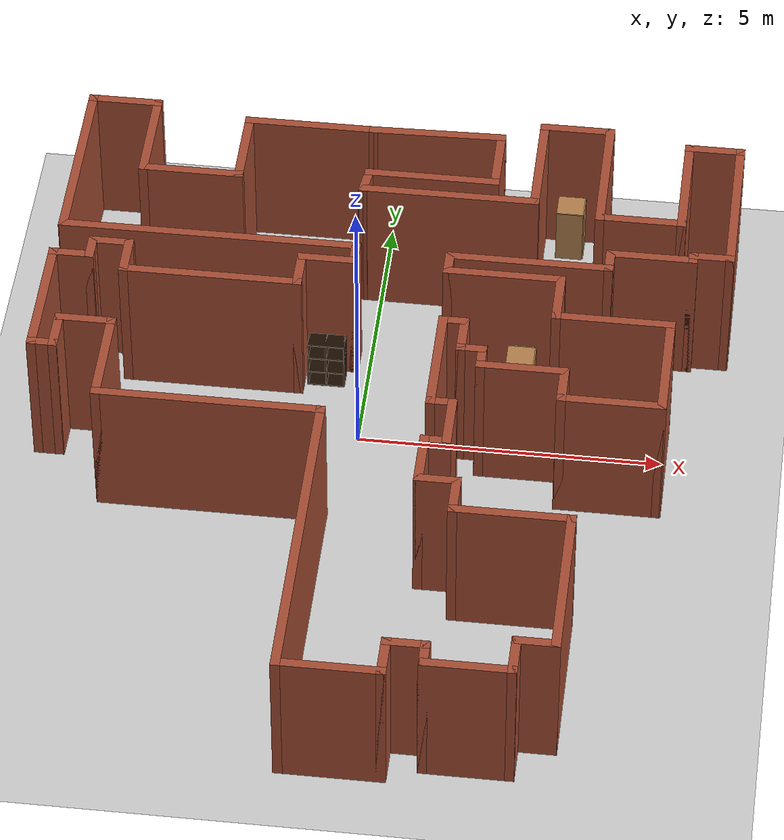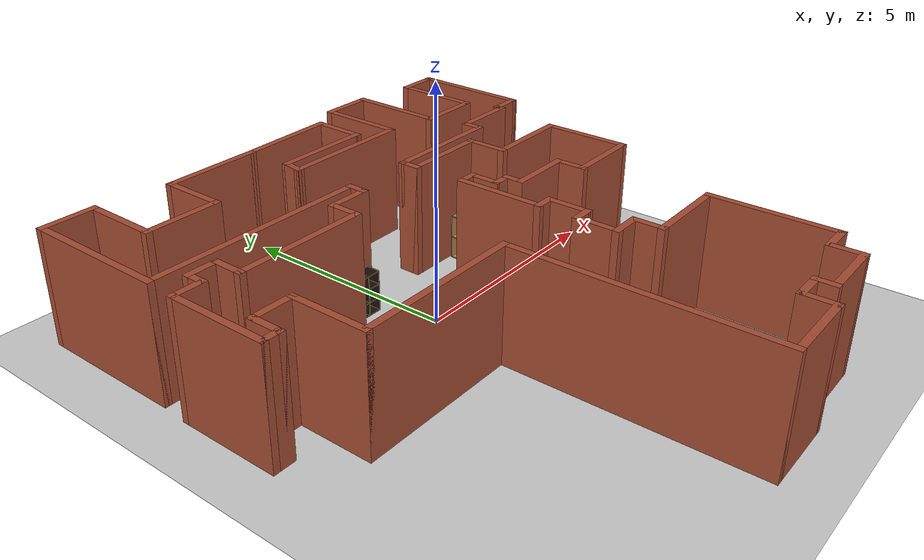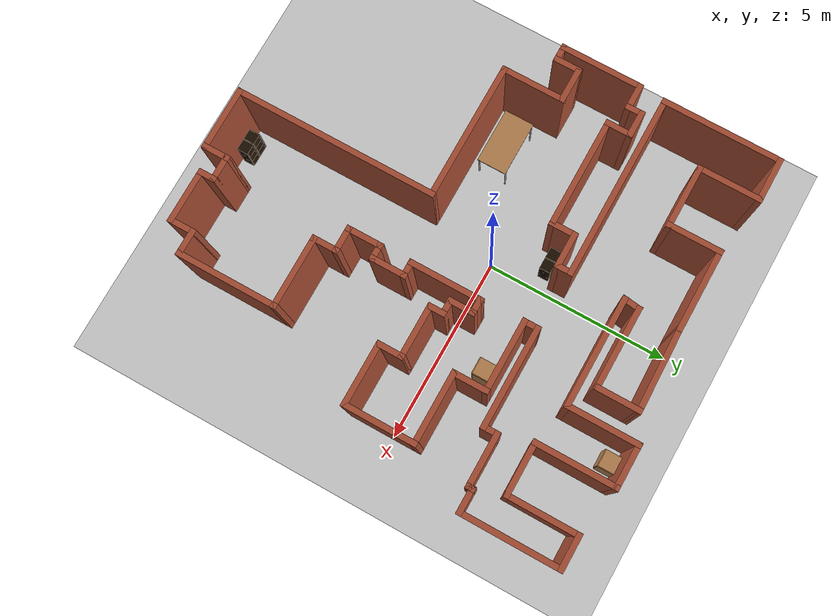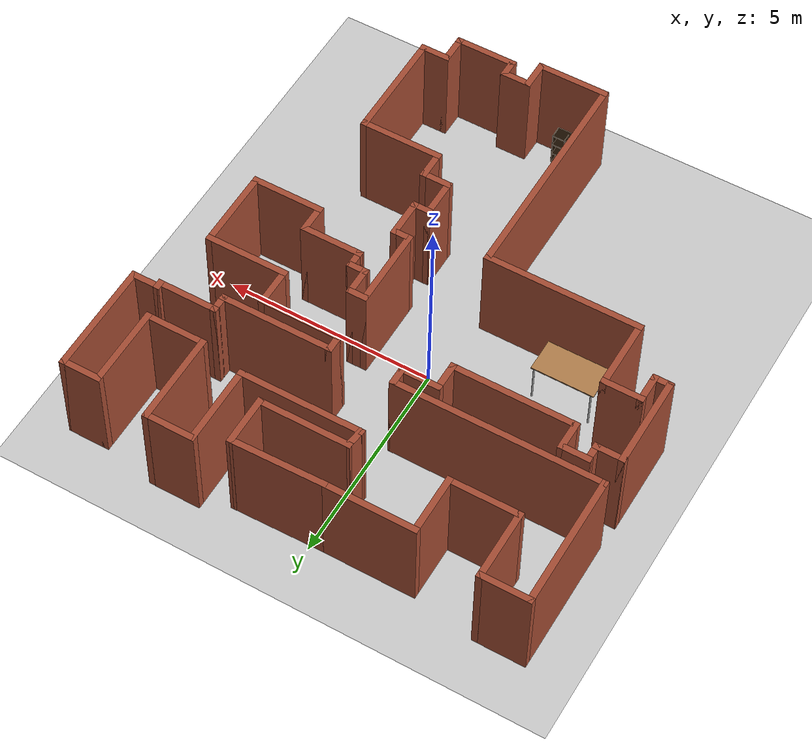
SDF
<sdf version="1.6">
 <world name="default">
  <light name="sun" type="directional">
   <pose>0 0 10 0 -0 0</pose>
   <diffuse>0.8 0.8 0.8 1</diffuse>
   <specular>0.2 0.2 0.2 1</specular>
   <attenuation>
    <range>1000</range>
    <constant>0.9</constant>
    <linear>0.01</linear>
    <quadratic>0.001</quadratic>
   </attenuation>
   <direction>-0.5 0.1 -0.9</direction>
  </light>
  <model name="ground_plane">
   <static>1</static>
   <link name="link">
    <collision name="collision">
     <geometry><plane><normal>0 0 1</normal><size>100 100</size></plane></geometry>
     <surface>
      <contact><collide_bitmask>65535</collide_bitmask></contact>
      <friction><ode><mu>100</mu><mu2>50</mu2></ode></friction>
     </surface>
    </collision>
    <visual name="visual">
     <cast_shadows>0</cast_shadows>
     <geometry><plane><normal>0 0 1</normal><size>100 100</size></plane></geometry>
     <material>
      <script><uri>file://media/materials/scripts/gazebo.material</uri><name>Gazebo/Grey</name></script>
     </material>
    </visual>
   </link>
  </model>
  <gravity>0 0 -9.8</gravity>
  <magnetic_field>6e-06 2.3e-05 -4.2e-05</magnetic_field>
  <atmosphere type="adiabatic"/>
  <physics name="default_physics" default="0" type="ode">
   <max_step_size>0.001</max_step_size>
   <real_time_factor>1</real_time_factor>
   <real_time_update_rate>1000</real_time_update_rate>
  </physics>
  <scene><ambient>0.4 0.4 0.4 1</ambient><background>0.7 0.7 0.7 1</background><shadows>1</shadows></scene>
  <audio><device>default</device></audio>
  <spherical_coordinates>
   <surface_model>EARTH_WGS84</surface_model>
   <latitude_deg>0</latitude_deg>
   <longitude_deg>0</longitude_deg>
   <elevation>0</elevation>
   <heading_deg>0</heading_deg>
  </spherical_coordinates>
  <model name="map_71">
   <pose>0.344292 -0.976267 0 0 -0 0</pose>
   <link name="Wall_0">
    <collision name="Wall_0_Collision">
     <geometry><box><size>2.25 0.15 2.5</size></box></geometry>
     <pose>0 0 1.25 0 -0 0</pose>
    </collision>
    <visual name="Wall_0_Visual">
     <pose>0 0 1.25 0 -0 0</pose>
     <geometry><box><size>2.25 0.15 2.5</size></box></geometry>
     <material>
      <script><uri>file://media/materials/scripts/gazebo.material</uri><name>Gazebo/Bricks</name></script>
      <ambient>1 1 1 1</ambient>
     </material>
     <meta><layer>0</layer></meta>
    </visual>
    <pose>-1.7 5.8 0 0 -0 3.14159</pose>
   </link>
   <link name="Wall_1">
    <collision name="Wall_1_Collision">
     <geometry><box><size>1.5 0.15 2.5</size></box></geometry>
     <pose>0 0 1.25 0 -0 0</pose>
    </collision>
    <visual name="Wall_1_Visual">
     <pose>0 0 1.25 0 -0 0</pose>
     <geometry><box><size>1.5 0.15 2.5</size></box></geometry>
     <material>
      <script><uri>file://media/materials/scripts/gazebo.material</uri><name>Gazebo/Bricks</name></script>
      <ambient>1 1 1 1</ambient>
     </material>
     <meta><layer>0</layer></meta>
    </visual>
    <pose>-2.75 5.125 0 0 -0 -1.5708</pose>
   </link>
   <link name="Wall_10">
    <collision name="Wall_10_Collision">
     <geometry><box><size>3 0.15 2.5</size></box></geometry>
     <pose>0 0 1.25 0 -0 0</pose>
    </collision>
    <visual name="Wall_10_Visual">
     <pose>0 0 1.25 0 -0 0</pose>
     <geometry><box><size>3 0.15 2.5</size></box></geometry>
     <material>
      <script><uri>file://media/materials/scripts/gazebo.material</uri><name>Gazebo/Bricks</name></script>
      <ambient>1 1 1 1</ambient>
     </material>
     <meta><layer>0</layer></meta>
    </visual>
    <pose>-2.875 2 0 0 -0 3.14159</pose>
   </link>
   <link name="Wall_11">
    <collision name="Wall_11_Collision">
     <geometry><box><size>0.75 0.15 2.5</size></box></geometry>
     <pose>0 0 1.25 0 -0 0</pose>
    </collision>
    <visual name="Wall_11_Visual">
     <pose>0 0 1.25 0 -0 0</pose>
     <geometry><box><size>0.75 0.15 2.5</size></box></geometry>
     <material>
      <script><uri>file://media/materials/scripts/gazebo.material</uri><name>Gazebo/Bricks</name></script>
      <ambient>1 1 1 1</ambient>
     </material>
     <meta><layer>0</layer></meta>
    </visual>
    <pose>-4.3 2.3 0 0 -0 1.5708</pose>
   </link>
   <link name="Wall_12">
    <collision name="Wall_12_Collision">
     <geometry><box><size>0.75 0.15 2.5</size></box></geometry>
     <pose>0 0 1.25 0 -0 0</pose>
    </collision>
    <visual name="Wall_12_Visual">
     <pose>0 0 1.25 0 -0 0</pose>
     <geometry><box><size>0.75 0.15 2.5</size></box></geometry>
     <material>
      <script><uri>file://media/materials/scripts/gazebo.material</uri><name>Gazebo/Bricks</name></script>
      <ambient>1 1 1 1</ambient>
     </material>
     <meta><layer>0</layer></meta>
    </visual>
    <pose>-4.6 2.6 0 0 -0 3.14159</pose>
   </link>
   <link name="Wall_13">
    <collision name="Wall_13_Collision">
     <geometry><box><size>0.5 0.15 2.5</size></box></geometry>
     <pose>0 0 1.25 0 -0 0</pose>
    </collision>
    <visual name="Wall_13_Visual">
     <pose>0 0 1.25 0 -0 0</pose>
     <geometry><box><size>0.5 0.15 2.5</size></box></geometry>
     <material>
      <script><uri>file://media/materials/scripts/gazebo.material</uri><name>Gazebo/Bricks</name></script>
      <ambient>1 1 1 1</ambient>
     </material>
     <meta><layer>0</layer></meta>
    </visual>
    <pose>-4.9 2.425 0 0 -0 -1.5708</pose>
   </link>
   <link name="Wall_18">
    <collision name="Wall_18_Collision">
     <geometry><box><size>0.75 0.15 2.5</size></box></geometry>
     <pose>0 0 1.25 0 -0 0</pose>
    </collision>
    <visual name="Wall_18_Visual">
     <pose>0 0 1.25 0 -0 0</pose>
     <geometry><box><size>0.75 0.15 2.5</size></box></geometry>
     <material>
      <script><uri>file://media/materials/scripts/gazebo.material</uri><name>Gazebo/Bricks</name></script>
      <ambient>1 1 1 1</ambient>
     </material>
     <meta><layer>0</layer></meta>
    </visual>
    <pose>-5.2 2.25 0 0 -0 3.14159</pose>
   </link>
   <link name="Wall_19">
    <collision name="Wall_19_Collision">
     <geometry><box><size>2.25 0.15 2.5</size></box></geometry>
     <pose>0 0 1.25 0 -0 0</pose>
    </collision>
    <visual name="Wall_19_Visual">
     <pose>0 0 1.25 0 -0 0</pose>
     <geometry><box><size>2.25 0.15 2.5</size></box></geometry>
     <material>
      <script><uri>file://media/materials/scripts/gazebo.material</uri><name>Gazebo/Bricks</name></script>
      <ambient>1 1 1 1</ambient>
     </material>
     <meta><layer>0</layer></meta>
    </visual>
    <pose>-5.5 1.2 0 0 -0 -1.5708</pose>
   </link>
   <link name="Wall_2">
    <collision name="Wall_2_Collision">
     <geometry><box><size>1.75 0.15 2.5</size></box></geometry>
     <pose>0 0 1.25 0 -0 0</pose>
    </collision>
    <visual name="Wall_2_Visual">
     <pose>0 0 1.25 0 -0 0</pose>
     <geometry><box><size>1.75 0.15 2.5</size></box></geometry>
     <material>
      <script><uri>file://media/materials/scripts/gazebo.material</uri><name>Gazebo/Bricks</name></script>
      <ambient>1 1 1 1</ambient>
     </material>
     <meta><layer>0</layer></meta>
    </visual>
    <pose>-3.55 4.45 0 0 -0 3.14159</pose>
   </link>
   <link name="Wall_20">
    <collision name="Wall_20_Collision">
     <geometry><box><size>0.5 0.15 2.5</size></box></geometry>
     <pose>0 0 1.25 0 -0 0</pose>
    </collision>
    <visual name="Wall_20_Visual">
     <pose>0 0 1.25 0 -0 0</pose>
     <geometry><box><size>0.5 0.15 2.5</size></box></geometry>
     <material>
      <script><uri>file://media/materials/scripts/gazebo.material</uri><name>Gazebo/Bricks</name></script>
      <ambient>1 1 1 1</ambient>
     </material>
     <meta><layer>0</layer></meta>
    </visual>
    <pose>-5.325 0.15 0 0 -0 0</pose>
   </link>
   <link name="Wall_21">
    <collision name="Wall_21_Collision">
     <geometry><box><size>0.75 0.15 2.5</size></box></geometry>
     <pose>0 0 1.25 0 -0 0</pose>
    </collision>
    <visual name="Wall_21_Visual">
     <pose>0 0 1.25 0 -0 0</pose>
     <geometry><box><size>0.75 0.15 2.5</size></box></geometry>
     <material>
      <script><uri>file://media/materials/scripts/gazebo.material</uri><name>Gazebo/Bricks</name></script>
      <ambient>1 1 1 1</ambient>
     </material>
     <meta><layer>0</layer></meta>
    </visual>
    <pose>-5.15 0.45 0 0 -0 1.5708</pose>
   </link>
   <link name="Wall_22">
    <collision name="Wall_22_Collision">
     <geometry><box><size>1 0.15 2.5</size></box></geometry>
     <pose>0 0 1.25 0 -0 0</pose>
    </collision>
    <visual name="Wall_22_Visual">
     <pose>0 0 1.25 0 -0 0</pose>
     <geometry><box><size>1 0.15 2.5</size></box></geometry>
     <material>
      <script><uri>file://media/materials/scripts/gazebo.material</uri><name>Gazebo/Bricks</name></script>
      <ambient>1 1 1 1</ambient>
     </material>
     <meta><layer>0</layer></meta>
    </visual>
    <pose>-4.725 0.75 0 0 -0 0</pose>
   </link>
   <link name="Wall_23">
    <collision name="Wall_23_Collision">
     <geometry><box><size>1.75 0.15 2.5</size></box></geometry>
     <pose>0 0 1.25 0 -0 0</pose>
    </collision>
    <visual name="Wall_23_Visual">
     <pose>0 0 1.25 0 -0 0</pose>
     <geometry><box><size>1.75 0.15 2.5</size></box></geometry>
     <material>
      <script><uri>file://media/materials/scripts/gazebo.material</uri><name>Gazebo/Bricks</name></script>
      <ambient>1 1 1 1</ambient>
     </material>
     <meta><layer>0</layer></meta>
    </visual>
    <pose>-4.3 -0.05 0 0 -0 -1.5708</pose>
   </link>
   <link name="Wall_24">
    <collision name="Wall_24_Collision">
     <geometry><box><size>3.75 0.15 2.5</size></box></geometry>
     <pose>0 0 1.25 0 -0 0</pose>
    </collision>
    <visual name="Wall_24_Visual">
     <pose>0 0 1.25 0 -0 0</pose>
     <geometry><box><size>3.75 0.15 2.5</size></box></geometry>
     <material>
      <script><uri>file://media/materials/scripts/gazebo.material</uri><name>Gazebo/Bricks</name></script>
      <ambient>1 1 1 1</ambient>
     </material>
     <meta><layer>0</layer></meta>
    </visual>
    <pose>-2.5 -0.85 0 0 -0 0</pose>
   </link>
   <link name="Wall_25">
    <collision name="Wall_25_Collision">
     <geometry><box><size>5.5 0.15 2.5</size></box></geometry>
     <pose>0 0 1.25 0 -0 0</pose>
    </collision>
    <visual name="Wall_25_Visual">
     <pose>0 0 1.25 0 -0 0</pose>
     <geometry><box><size>5.5 0.15 2.5</size></box></geometry>
     <material>
      <script><uri>file://media/materials/scripts/gazebo.material</uri><name>Gazebo/Bricks</name></script>
      <ambient>1 1 1 1</ambient>
     </material>
     <meta><layer>0</layer></meta>
    </visual>
    <pose>-0.7 -3.525 0 0 -0 -1.5708</pose>
   </link>
   <link name="Wall_26">
    <collision name="Wall_26_Collision">
     <geometry><box><size>1.75 0.15 2.5</size></box></geometry>
     <pose>0 0 1.25 0 -0 0</pose>
    </collision>
    <visual name="Wall_26_Visual">
     <pose>0 0 1.25 0 -0 0</pose>
     <geometry><box><size>1.75 0.15 2.5</size></box></geometry>
     <material>
      <script><uri>file://media/materials/scripts/gazebo.material</uri><name>Gazebo/Bricks</name></script>
      <ambient>1 1 1 1</ambient>
     </material>
     <meta><layer>0</layer></meta>
    </visual>
    <pose>0.1 -6.2 0 0 -0 0</pose>
   </link>
   <link name="Wall_27">
    <collision name="Wall_27_Collision">
     <geometry><box><size>0.75 0.15 2.5</size></box></geometry>
     <pose>0 0 1.25 0 -0 0</pose>
    </collision>
    <visual name="Wall_27_Visual">
     <pose>0 0 1.25 0 -0 0</pose>
     <geometry><box><size>0.75 0.15 2.5</size></box></geometry>
     <material>
      <script><uri>file://media/materials/scripts/gazebo.material</uri><name>Gazebo/Bricks</name></script>
      <ambient>1 1 1 1</ambient>
     </material>
     <meta><layer>0</layer></meta>
    </visual>
    <pose>0.9 -5.9 0 0 -0 1.5708</pose>
   </link>
   <link name="Wall_28">
    <collision name="Wall_28_Collision">
     <geometry><box><size>0.75 0.15 2.5</size></box></geometry>
     <pose>0 0 1.25 0 -0 0</pose>
    </collision>
    <visual name="Wall_28_Visual">
     <pose>0 0 1.25 0 -0 0</pose>
     <geometry><box><size>0.75 0.15 2.5</size></box></geometry>
     <material>
      <script><uri>file://media/materials/scripts/gazebo.material</uri><name>Gazebo/Bricks</name></script>
      <ambient>1 1 1 1</ambient>
     </material>
     <meta><layer>0</layer></meta>
    </visual>
    <pose>1.2 -5.6 0 0 -0 0</pose>
   </link>
   <link name="Wall_29">
    <collision name="Wall_29_Collision">
     <geometry><box><size>0.5 0.15 2.5</size></box></geometry>
     <pose>0 0 1.25 0 -0 0</pose>
    </collision>
    <visual name="Wall_29_Visual">
     <pose>0 0 1.25 0 -0 0</pose>
     <geometry><box><size>0.5 0.15 2.5</size></box></geometry>
     <material>
      <script><uri>file://media/materials/scripts/gazebo.material</uri><name>Gazebo/Bricks</name></script>
      <ambient>1 1 1 1</ambient>
     </material>
     <meta><layer>0</layer></meta>
    </visual>
    <pose>1.5 -5.775 0 0 -0 -1.5708</pose>
   </link>
   <link name="Wall_3">
    <collision name="Wall_3_Collision">
     <geometry><box><size>1.75 0.15 2.5</size></box></geometry>
     <pose>0 0 1.25 0 -0 0</pose>
    </collision>
    <visual name="Wall_3_Visual">
     <pose>0 0 1.25 0 -0 0</pose>
     <geometry><box><size>1.75 0.15 2.5</size></box></geometry>
     <material>
      <script><uri>file://media/materials/scripts/gazebo.material</uri><name>Gazebo/Bricks</name></script>
      <ambient>1 1 1 1</ambient>
     </material>
     <meta><layer>0</layer></meta>
    </visual>
    <pose>-4.35 5.25 0 0 -0 1.5708</pose>
   </link>
   <link name="Wall_30">
    <collision name="Wall_30_Collision">
     <geometry><box><size>1.5 0.15 2.5</size></box></geometry>
     <pose>0 0 1.25 0 -0 0</pose>
    </collision>
    <visual name="Wall_30_Visual">
     <pose>0 0 1.25 0 -0 0</pose>
     <geometry><box><size>1.5 0.15 2.5</size></box></geometry>
     <material>
      <script><uri>file://media/materials/scripts/gazebo.material</uri><name>Gazebo/Bricks</name></script>
      <ambient>1 1 1 1</ambient>
     </material>
     <meta><layer>0</layer></meta>
    </visual>
    <pose>2.175 -5.95 0 0 -0 0</pose>
   </link>
   <link name="Wall_31">
    <collision name="Wall_31_Collision">
     <geometry><box><size>0.75 0.15 2.5</size></box></geometry>
     <pose>0 0 1.25 0 -0 0</pose>
    </collision>
    <visual name="Wall_31_Visual">
     <pose>0 0 1.25 0 -0 0</pose>
     <geometry><box><size>0.75 0.15 2.5</size></box></geometry>
     <material>
      <script><uri>file://media/materials/scripts/gazebo.material</uri><name>Gazebo/Bricks</name></script>
      <ambient>1 1 1 1</ambient>
     </material>
     <meta><layer>0</layer></meta>
    </visual>
    <pose>2.85 -5.65 0 0 -0 1.5708</pose>
   </link>
   <link name="Wall_32">
    <collision name="Wall_32_Collision">
     <geometry><box><size>0.75 0.15 2.5</size></box></geometry>
     <pose>0 0 1.25 0 -0 0</pose>
    </collision>
    <visual name="Wall_32_Visual">
     <pose>0 0 1.25 0 -0 0</pose>
     <geometry><box><size>0.75 0.15 2.5</size></box></geometry>
     <material>
      <script><uri>file://media/materials/scripts/gazebo.material</uri><name>Gazebo/Bricks</name></script>
      <ambient>1 1 1 1</ambient>
     </material>
     <meta><layer>0</layer></meta>
    </visual>
    <pose>3.15 -5.35 0 0 -0 0</pose>
   </link>
   <link name="Wall_33">
    <collision name="Wall_33_Collision">
     <geometry><box><size>2.75 0.15 2.5</size></box></geometry>
     <pose>0 0 1.25 0 -0 0</pose>
    </collision>
    <visual name="Wall_33_Visual">
     <pose>0 0 1.25 0 -0 0</pose>
     <geometry><box><size>2.75 0.15 2.5</size></box></geometry>
     <material>
      <script><uri>file://media/materials/scripts/gazebo.material</uri><name>Gazebo/Bricks</name></script>
      <ambient>1 1 1 1</ambient>
     </material>
     <meta><layer>0</layer></meta>
    </visual>
    <pose>3.45 -4.05 0 0 -0 1.5708</pose>
   </link>
   <link name="Wall_34">
    <collision name="Wall_34_Collision">
     <geometry><box><size>2 0.15 2.5</size></box></geometry>
     <pose>0 0 1.25 0 -0 0</pose>
    </collision>
    <visual name="Wall_34_Visual">
     <pose>0 0 1.25 0 -0 0</pose>
     <geometry><box><size>2 0.15 2.5</size></box></geometry>
     <material>
      <script><uri>file://media/materials/scripts/gazebo.material</uri><name>Gazebo/Bricks</name></script>
      <ambient>1 1 1 1</ambient>
     </material>
     <meta><layer>0</layer></meta>
    </visual>
    <pose>2.525 -2.75 0 0 -0 3.14159</pose>
   </link>
   <link name="Wall_35">
    <collision name="Wall_35_Collision">
     <geometry><box><size>0.75 0.15 2.5</size></box></geometry>
     <pose>0 0 1.25 0 -0 0</pose>
    </collision>
    <visual name="Wall_35_Visual">
     <pose>0 0 1.25 0 -0 0</pose>
     <geometry><box><size>0.75 0.15 2.5</size></box></geometry>
     <material>
      <script><uri>file://media/materials/scripts/gazebo.material</uri><name>Gazebo/Bricks</name></script>
      <ambient>1 1 1 1</ambient>
     </material>
     <meta><layer>0</layer></meta>
    </visual>
    <pose>1.6 -2.45 0 0 -0 1.5708</pose>
   </link>
   <link name="Wall_36">
    <collision name="Wall_36_Collision">
     <geometry><box><size>0.75 0.15 2.5</size></box></geometry>
     <pose>0 0 1.25 0 -0 0</pose>
    </collision>
    <visual name="Wall_36_Visual">
     <pose>0 0 1.25 0 -0 0</pose>
     <geometry><box><size>0.75 0.15 2.5</size></box></geometry>
     <material>
      <script><uri>file://media/materials/scripts/gazebo.material</uri><name>Gazebo/Bricks</name></script>
      <ambient>1 1 1 1</ambient>
     </material>
     <meta><layer>0</layer></meta>
    </visual>
    <pose>1.3 -2.15 0 0 -0 3.14159</pose>
   </link>
   <link name="Wall_37">
    <collision name="Wall_37_Collision">
     <geometry><box><size>1 0.15 2.5</size></box></geometry>
     <pose>0 0 1.25 0 -0 0</pose>
    </collision>
    <visual name="Wall_37_Visual">
     <pose>0 0 1.25 0 -0 0</pose>
     <geometry><box><size>1 0.15 2.5</size></box></geometry>
     <material>
      <script><uri>file://media/materials/scripts/gazebo.material</uri><name>Gazebo/Bricks</name></script>
      <ambient>1 1 1 1</ambient>
     </material>
     <meta><layer>0</layer></meta>
    </visual>
    <pose>1 -1.725 0 0 -0 1.5708</pose>
   </link>
   <link name="Wall_38">
    <collision name="Wall_38_Collision">
     <geometry><box><size>0.5 0.15 2.5</size></box></geometry>
     <pose>0 0 1.25 0 -0 0</pose>
    </collision>
    <visual name="Wall_38_Visual">
     <pose>0 0 1.25 0 -0 0</pose>
     <geometry><box><size>0.5 0.15 2.5</size></box></geometry>
     <material>
      <script><uri>file://media/materials/scripts/gazebo.material</uri><name>Gazebo/Bricks</name></script>
      <ambient>1 1 1 1</ambient>
     </material>
     <meta><layer>0</layer></meta>
    </visual>
    <pose>1.175 -1.3 0 0 -0 0</pose>
   </link>
   <link name="Wall_39">
    <collision name="Wall_39_Collision">
     <geometry><box><size>1 0.15 2.5</size></box></geometry>
     <pose>0 0 1.25 0 -0 0</pose>
    </collision>
    <visual name="Wall_39_Visual">
     <pose>0 0 1.25 0 -0 0</pose>
     <geometry><box><size>1 0.15 2.5</size></box></geometry>
     <material>
      <script><uri>file://media/materials/scripts/gazebo.material</uri><name>Gazebo/Bricks</name></script>
      <ambient>1 1 1 1</ambient>
     </material>
     <meta><layer>0</layer></meta>
    </visual>
    <pose>1.35 -0.875 0 0 -0 1.5708</pose>
   </link>
   <link name="Wall_4">
    <collision name="Wall_4_Collision">
     <geometry><box><size>1.25 0.15 2.5</size></box></geometry>
     <pose>0 0 1.25 0 -0 0</pose>
    </collision>
    <visual name="Wall_4_Visual">
     <pose>0 0 1.25 0 -0 0</pose>
     <geometry><box><size>1.25 0.15 2.5</size></box></geometry>
     <material>
      <script><uri>file://media/materials/scripts/gazebo.material</uri><name>Gazebo/Bricks</name></script>
      <ambient>1 1 1 1</ambient>
     </material>
     <meta><layer>0</layer></meta>
    </visual>
    <pose>-4.9 6.05 0 0 -0 3.14159</pose>
   </link>
   <link name="Wall_40">
    <collision name="Wall_40_Collision">
     <geometry><box><size>0.5 0.15 2.5</size></box></geometry>
     <pose>0 0 1.25 0 -0 0</pose>
    </collision>
    <visual name="Wall_40_Visual">
     <pose>0 0 1.25 0 -0 0</pose>
     <geometry><box><size>0.5 0.15 2.5</size></box></geometry>
     <material>
      <script><uri>file://media/materials/scripts/gazebo.material</uri><name>Gazebo/Bricks</name></script>
      <ambient>1 1 1 1</ambient>
     </material>
     <meta><layer>0</layer></meta>
    </visual>
    <pose>1.175 -0.45 0 0 -0 3.14159</pose>
   </link>
   <link name="Wall_41">
    <collision name="Wall_41_Collision">
     <geometry><box><size>2 0.15 2.5</size></box></geometry>
     <pose>0 0 1.25 0 -0 0</pose>
    </collision>
    <visual name="Wall_41_Visual">
     <pose>0 0 1.25 0 -0 0</pose>
     <geometry><box><size>2 0.15 2.5</size></box></geometry>
     <material>
      <script><uri>file://media/materials/scripts/gazebo.material</uri><name>Gazebo/Bricks</name></script>
      <ambient>1 1 1 1</ambient>
     </material>
     <meta><layer>0</layer></meta>
    </visual>
    <pose>1 0.475 0 0 -0 1.5708</pose>
   </link>
   <link name="Wall_42">
    <collision name="Wall_42_Collision">
     <geometry><box><size>0.5 0.15 2.5</size></box></geometry>
     <pose>0 0 1.25 0 -0 0</pose>
    </collision>
    <visual name="Wall_42_Visual">
     <pose>0 0 1.25 0 -0 0</pose>
     <geometry><box><size>0.5 0.15 2.5</size></box></geometry>
     <material>
      <script><uri>file://media/materials/scripts/gazebo.material</uri><name>Gazebo/Bricks</name></script>
      <ambient>1 1 1 1</ambient>
     </material>
     <meta><layer>0</layer></meta>
    </visual>
    <pose>1.175 1.4 0 0 -0 0</pose>
   </link>
   <link name="Wall_43">
    <collision name="Wall_43_Collision">
     <geometry><box><size>0.75 0.15 2.5</size></box></geometry>
     <pose>0 0 1.25 0 -0 0</pose>
    </collision>
    <visual name="Wall_43_Visual">
     <pose>0 0 1.25 0 -0 0</pose>
     <geometry><box><size>0.75 0.15 2.5</size></box></geometry>
     <material>
      <script><uri>file://media/materials/scripts/gazebo.material</uri><name>Gazebo/Bricks</name></script>
      <ambient>1 1 1 1</ambient>
     </material>
     <meta><layer>0</layer></meta>
    </visual>
    <pose>1.35 1.1 0 0 -0 -1.5708</pose>
   </link>
   <link name="Wall_44">
    <collision name="Wall_44_Collision">
     <geometry><box><size>0.5 0.15 2.5</size></box></geometry>
     <pose>0 0 1.25 0 -0 0</pose>
    </collision>
    <visual name="Wall_44_Visual">
     <pose>0 0 1.25 0 -0 0</pose>
     <geometry><box><size>0.5 0.15 2.5</size></box></geometry>
     <material>
      <script><uri>file://media/materials/scripts/gazebo.material</uri><name>Gazebo/Bricks</name></script>
      <ambient>1 1 1 1</ambient>
     </material>
     <meta><layer>0</layer></meta>
    </visual>
    <pose>1.525 0.8 0 0 -0 0</pose>
   </link>
   <link name="Wall_45">
    <collision name="Wall_45_Collision">
     <geometry><box><size>0.5 0.15 2.5</size></box></geometry>
     <pose>0 0 1.25 0 -0 0</pose>
    </collision>
    <visual name="Wall_45_Visual">
     <pose>0 0 1.25 0 -0 0</pose>
     <geometry><box><size>0.5 0.15 2.5</size></box></geometry>
     <material>
      <script><uri>file://media/materials/scripts/gazebo.material</uri><name>Gazebo/Bricks</name></script>
      <ambient>1 1 1 1</ambient>
     </material>
     <meta><layer>0</layer></meta>
    </visual>
    <pose>1.7 0.625 0 0 -0 -1.5708</pose>
   </link>
   <link name="Wall_46">
    <collision name="Wall_46_Collision">
     <geometry><box><size>1.5 0.15 2.5</size></box></geometry>
     <pose>0 0 1.25 0 -0 0</pose>
    </collision>
    <visual name="Wall_46_Visual">
     <pose>0 0 1.25 0 -0 0</pose>
     <geometry><box><size>1.5 0.15 2.5</size></box></geometry>
     <material>
      <script><uri>file://media/materials/scripts/gazebo.material</uri><name>Gazebo/Bricks</name></script>
      <ambient>1 1 1 1</ambient>
     </material>
     <meta><layer>0</layer></meta>
    </visual>
    <pose>2.375 0.45 0 0 -0 0</pose>
   </link>
   <link name="Wall_47">
    <collision name="Wall_47_Collision">
     <geometry><box><size>0.75 0.15 2.5</size></box></geometry>
     <pose>0 0 1.25 0 -0 0</pose>
    </collision>
    <visual name="Wall_47_Visual">
     <pose>0 0 1.25 0 -0 0</pose>
     <geometry><box><size>0.75 0.15 2.5</size></box></geometry>
     <material>
      <script><uri>file://media/materials/scripts/gazebo.material</uri><name>Gazebo/Bricks</name></script>
      <ambient>1 1 1 1</ambient>
     </material>
     <meta><layer>0</layer></meta>
    </visual>
    <pose>3.05 0.15 0 0 -0 -1.5708</pose>
   </link>
   <link name="Wall_48">
    <collision name="Wall_48_Collision">
     <geometry><box><size>1.75 0.15 2.5</size></box></geometry>
     <pose>0 0 1.25 0 -0 0</pose>
    </collision>
    <visual name="Wall_48_Visual">
     <pose>0 0 1.25 0 -0 0</pose>
     <geometry><box><size>1.75 0.15 2.5</size></box></geometry>
     <material>
      <script><uri>file://media/materials/scripts/gazebo.material</uri><name>Gazebo/Bricks</name></script>
      <ambient>1 1 1 1</ambient>
     </material>
     <meta><layer>0</layer></meta>
    </visual>
    <pose>3.85 -0.15 0 0 -0 0</pose>
   </link>
   <link name="Wall_49">
    <collision name="Wall_49_Collision">
     <geometry><box><size>2 0.15 2.5</size></box></geometry>
     <pose>0 0 1.25 0 -0 0</pose>
    </collision>
    <visual name="Wall_49_Visual">
     <pose>0 0 1.25 0 -0 0</pose>
     <geometry><box><size>2 0.15 2.5</size></box></geometry>
     <material>
      <script><uri>file://media/materials/scripts/gazebo.material</uri><name>Gazebo/Bricks</name></script>
      <ambient>1 1 1 1</ambient>
     </material>
     <meta><layer>0</layer></meta>
    </visual>
    <pose>4.65 0.775 0 0 -0 1.5708</pose>
   </link>
   <link name="Wall_5">
    <collision name="Wall_5_Collision">
     <geometry><box><size>3.25 0.15 2.5</size></box></geometry>
     <pose>0 0 1.25 0 -0 0</pose>
    </collision>
    <visual name="Wall_5_Visual">
     <pose>0 0 1.25 0 -0 0</pose>
     <geometry><box><size>3.25 0.15 2.5</size></box></geometry>
     <material>
      <script><uri>file://media/materials/scripts/gazebo.material</uri><name>Gazebo/Bricks</name></script>
      <ambient>1 1 1 1</ambient>
     </material>
     <meta><layer>0</layer></meta>
    </visual>
    <pose>-5.45 4.5 0 0 -0 -1.5708</pose>
   </link>
   <link name="Wall_50">
    <collision name="Wall_50_Collision">
     <geometry><box><size>2 0.15 2.5</size></box></geometry>
     <pose>0 0 1.25 0 -0 0</pose>
    </collision>
    <visual name="Wall_50_Visual">
     <pose>0 0 1.25 0 -0 0</pose>
     <geometry><box><size>2 0.15 2.5</size></box></geometry>
     <material>
      <script><uri>file://media/materials/scripts/gazebo.material</uri><name>Gazebo/Bricks</name></script>
      <ambient>1 1 1 1</ambient>
     </material>
     <meta><layer>0</layer></meta>
    </visual>
    <pose>3.725 1.7 0 0 -0 3.14159</pose>
   </link>
   <link name="Wall_51">
    <collision name="Wall_51_Collision">
     <geometry><box><size>1 0.15 2.5</size></box></geometry>
     <pose>0 0 1.25 0 -0 0</pose>
    </collision>
    <visual name="Wall_51_Visual">
     <pose>0 0 1.25 0 -0 0</pose>
     <geometry><box><size>1 0.15 2.5</size></box></geometry>
     <material>
      <script><uri>file://media/materials/scripts/gazebo.material</uri><name>Gazebo/Bricks</name></script>
      <ambient>1 1 1 1</ambient>
     </material>
     <meta><layer>0</layer></meta>
    </visual>
    <pose>2.8 2.125 0 0 -0 1.5708</pose>
   </link>
   <link name="Wall_52">
    <collision name="Wall_52_Collision">
     <geometry><box><size>2 0.15 2.5</size></box></geometry>
     <pose>0 0 1.25 0 -0 0</pose>
    </collision>
    <visual name="Wall_52_Visual">
     <pose>0 0 1.25 0 -0 0</pose>
     <geometry><box><size>2 0.15 2.5</size></box></geometry>
     <material>
      <script><uri>file://media/materials/scripts/gazebo.material</uri><name>Gazebo/Bricks</name></script>
      <ambient>1 1 1 1</ambient>
     </material>
     <meta><layer>0</layer></meta>
    </visual>
    <pose>1.875 2.55 0 0 -0 3.14159</pose>
   </link>
   <link name="Wall_53">
    <collision name="Wall_53_Collision">
     <geometry><box><size>0.5 0.15 2.5</size></box></geometry>
     <pose>0 0 1.25 0 -0 0</pose>
    </collision>
    <visual name="Wall_53_Visual">
     <pose>0 0 1.25 0 -0 0</pose>
     <geometry><box><size>0.5 0.15 2.5</size></box></geometry>
     <material>
      <script><uri>file://media/materials/scripts/gazebo.material</uri><name>Gazebo/Bricks</name></script>
      <ambient>1 1 1 1</ambient>
     </material>
     <meta><layer>0</layer></meta>
    </visual>
    <pose>0.95 2.725 0 0 -0 1.5708</pose>
   </link>
   <link name="Wall_54">
    <collision name="Wall_54_Collision">
     <geometry><box><size>2.75 0.15 2.5</size></box></geometry>
     <pose>0 0 1.25 0 -0 0</pose>
    </collision>
    <visual name="Wall_54_Visual">
     <pose>0 0 1.25 0 -0 0</pose>
     <geometry><box><size>2.75 0.15 2.5</size></box></geometry>
     <material>
      <script><uri>file://media/materials/scripts/gazebo.material</uri><name>Gazebo/Bricks</name></script>
      <ambient>1 1 1 1</ambient>
     </material>
     <meta><layer>0</layer></meta>
    </visual>
    <pose>2.25 2.9 0 0 -0 0</pose>
   </link>
   <link name="Wall_55">
    <collision name="Wall_55_Collision">
     <geometry><box><size>0.5 0.15 2.5</size></box></geometry>
     <pose>0 0 1.25 0 -0 0</pose>
    </collision>
    <visual name="Wall_55_Visual">
     <pose>0 0 1.25 0 -0 0</pose>
     <geometry><box><size>0.5 0.15 2.5</size></box></geometry>
     <material>
      <script><uri>file://media/materials/scripts/gazebo.material</uri><name>Gazebo/Bricks</name></script>
      <ambient>1 1 1 1</ambient>
     </material>
     <meta><layer>0</layer></meta>
    </visual>
    <pose>3.55 3.075 0 0 -0 1.5708</pose>
   </link>
   <link name="Wall_56">
    <collision name="Wall_56_Collision">
     <geometry><box><size>1.5 0.15 2.5</size></box></geometry>
     <pose>0 0 1.25 0 -0 0</pose>
    </collision>
    <visual name="Wall_56_Visual">
     <pose>0 0 1.25 0 -0 0</pose>
     <geometry><box><size>1.5 0.15 2.5</size></box></geometry>
     <material>
      <script><uri>file://media/materials/scripts/gazebo.material</uri><name>Gazebo/Bricks</name></script>
      <ambient>1 1 1 1</ambient>
     </material>
     <meta><layer>0</layer></meta>
    </visual>
    <pose>4.225 3.25 0 0 -0 0</pose>
   </link>
   <link name="Wall_57">
    <collision name="Wall_57_Collision">
     <geometry><box><size>0.25 0.15 2.5</size></box></geometry>
     <pose>0 0 1.25 0 -0 0</pose>
    </collision>
    <visual name="Wall_57_Visual">
     <pose>0 0 1.25 0 -0 0</pose>
     <geometry><box><size>0.25 0.15 2.5</size></box></geometry>
     <material>
      <script><uri>file://media/materials/scripts/gazebo.material</uri><name>Gazebo/Bricks</name></script>
      <ambient>1 1 1 1</ambient>
     </material>
     <meta><layer>0</layer></meta>
    </visual>
    <pose>4.9 3.3 0 0 -0 1.5708</pose>
   </link>
   <link name="Wall_58">
    <collision name="Wall_58_Collision">
     <geometry><box><size>0.75 0.15 2.5</size></box></geometry>
     <pose>0 0 1.25 0 -0 0</pose>
    </collision>
    <visual name="Wall_58_Visual">
     <pose>0 0 1.25 0 -0 0</pose>
     <geometry><box><size>0.75 0.15 2.5</size></box></geometry>
     <material>
      <script><uri>file://media/materials/scripts/gazebo.material</uri><name>Gazebo/Bricks</name></script>
      <ambient>1 1 1 1</ambient>
     </material>
     <meta><layer>0</layer></meta>
    </visual>
    <pose>5.2 3.35 0 0 -0 0</pose>
   </link>
   <link name="Wall_59">
    <collision name="Wall_59_Collision">
     <geometry><box><size>2.75 0.15 2.5</size></box></geometry>
     <pose>0 0 1.25 0 -0 0</pose>
    </collision>
    <visual name="Wall_59_Visual">
     <pose>0 0 1.25 0 -0 0</pose>
     <geometry><box><size>2.75 0.15 2.5</size></box></geometry>
     <material>
      <script><uri>file://media/materials/scripts/gazebo.material</uri><name>Gazebo/Bricks</name></script>
      <ambient>1 1 1 1</ambient>
     </material>
     <meta><layer>0</layer></meta>
    </visual>
    <pose>5.5 4.65 0 0 -0 1.5708</pose>
   </link>
   <link name="Wall_6">
    <collision name="Wall_6_Collision">
     <geometry><box><size>5 0.15 2.5</size></box></geometry>
     <pose>0 0 1.25 0 -0 0</pose>
    </collision>
    <visual name="Wall_6_Visual">
     <pose>0 0 1.25 0 -0 0</pose>
     <geometry><box><size>5 0.15 2.5</size></box></geometry>
     <material>
      <script><uri>file://media/materials/scripts/gazebo.material</uri><name>Gazebo/Bricks</name></script>
      <ambient>1 1 1 1</ambient>
     </material>
     <meta><layer>0</layer></meta>
    </visual>
    <pose>-3.025 2.95 0 0 -0 0</pose>
   </link>
   <link name="Wall_60">
    <collision name="Wall_60_Collision">
     <geometry><box><size>1 0.15 2.5</size></box></geometry>
     <pose>0 0 1.25 0 -0 0</pose>
    </collision>
    <visual name="Wall_60_Visual">
     <pose>0 0 1.25 0 -0 0</pose>
     <geometry><box><size>1 0.15 2.5</size></box></geometry>
     <material>
      <script><uri>file://media/materials/scripts/gazebo.material</uri><name>Gazebo/Bricks</name></script>
      <ambient>1 1 1 1</ambient>
     </material>
     <meta><layer>0</layer></meta>
    </visual>
    <pose>5.075 5.95 0 0 -0 3.14159</pose>
   </link>
   <link name="Wall_62">
    <collision name="Wall_62_Collision">
     <geometry><box><size>2 0.15 2.5</size></box></geometry>
     <pose>0 0 1.25 0 -0 0</pose>
    </collision>
    <visual name="Wall_62_Visual">
     <pose>0 0 1.25 0 -0 0</pose>
     <geometry><box><size>2 0.15 2.5</size></box></geometry>
     <material>
      <script><uri>file://media/materials/scripts/gazebo.material</uri><name>Gazebo/Bricks</name></script>
      <ambient>1 1 1 1</ambient>
     </material>
     <meta><layer>0</layer></meta>
    </visual>
    <pose>4.65 5.025 0 0 -0 -1.5708</pose>
   </link>
   <link name="Wall_63">
    <collision name="Wall_63_Collision">
     <geometry><box><size>1.5 0.15 2.5</size></box></geometry>
     <pose>0 0 1.25 0 -0 0</pose>
    </collision>
    <visual name="Wall_63_Visual">
     <pose>0 0 1.25 0 -0 0</pose>
     <geometry><box><size>1.5 0.15 2.5</size></box></geometry>
     <material>
      <script><uri>file://media/materials/scripts/gazebo.material</uri><name>Gazebo/Bricks</name></script>
      <ambient>1 1 1 1</ambient>
     </material>
     <meta><layer>0</layer></meta>
    </visual>
    <pose>3.975 4.1 0 0 -0 3.14159</pose>
   </link>
   <link name="Wall_64">
    <collision name="Wall_64_Collision">
     <geometry><box><size>2.25 0.15 2.5</size></box></geometry>
     <pose>0 0 1.25 0 -0 0</pose>
    </collision>
    <visual name="Wall_64_Visual">
     <pose>0 0 1.25 0 -0 0</pose>
     <geometry><box><size>2.25 0.15 2.5</size></box></geometry>
     <material>
      <script><uri>file://media/materials/scripts/gazebo.material</uri><name>Gazebo/Bricks</name></script>
      <ambient>1 1 1 1</ambient>
     </material>
     <meta><layer>0</layer></meta>
    </visual>
    <pose>3.3 5.15 0 0 -0 1.5708</pose>
   </link>
   <link name="Wall_65">
    <collision name="Wall_65_Collision">
     <geometry><box><size>1.25 0.15 2.5</size></box></geometry>
     <pose>0 0 1.25 0 -0 0</pose>
    </collision>
    <visual name="Wall_65_Visual">
     <pose>0 0 1.25 0 -0 0</pose>
     <geometry><box><size>1.25 0.15 2.5</size></box></geometry>
     <material>
      <script><uri>file://media/materials/scripts/gazebo.material</uri><name>Gazebo/Bricks</name></script>
      <ambient>1 1 1 1</ambient>
     </material>
     <meta><layer>0</layer></meta>
    </visual>
    <pose>2.75 6.2 0 0 -0 3.14159</pose>
   </link>
   <link name="Wall_66">
    <collision name="Wall_66_Collision">
     <geometry><box><size>2 0.15 2.5</size></box></geometry>
     <pose>0 0 1.25 0 -0 0</pose>
    </collision>
    <visual name="Wall_66_Visual">
     <pose>0 0 1.25 0 -0 0</pose>
     <geometry><box><size>2 0.15 2.5</size></box></geometry>
     <material>
      <script><uri>file://media/materials/scripts/gazebo.material</uri><name>Gazebo/Bricks</name></script>
      <ambient>1 1 1 1</ambient>
     </material>
     <meta><layer>0</layer></meta>
    </visual>
    <pose>2.2 5.275 0 0 -0 -1.5708</pose>
   </link>
   <link name="Wall_7">
    <collision name="Wall_7_Collision">
     <geometry><box><size>0.5 0.15 2.5</size></box></geometry>
     <pose>0 0 1.25 0 -0 0</pose>
    </collision>
    <visual name="Wall_7_Visual">
     <pose>0 0 1.25 0 -0 0</pose>
     <geometry><box><size>0.5 0.15 2.5</size></box></geometry>
     <material>
      <script><uri>file://media/materials/scripts/gazebo.material</uri><name>Gazebo/Bricks</name></script>
      <ambient>1 1 1 1</ambient>
     </material>
     <meta><layer>0</layer></meta>
    </visual>
    <pose>-0.6 2.775 0 0 -0 -1.5708</pose>
   </link>
   <link name="Wall_73">
    <collision name="Wall_73_Collision">
     <geometry><box><size>2.25 0.15 2.5</size></box></geometry>
     <pose>0 0 1.25 0 -0 0</pose>
    </collision>
    <visual name="Wall_73_Visual">
     <pose>0 0 1.25 0 -0 0</pose>
     <geometry><box><size>2.25 0.15 2.5</size></box></geometry>
     <material>
      <script><uri>file://media/materials/scripts/gazebo.material</uri><name>Gazebo/Bricks</name></script>
      <ambient>1 1 1 1</ambient>
     </material>
     <meta><layer>0</layer></meta>
    </visual>
    <pose>0.45 4.75 0 0 -0 0</pose>
   </link>
   <link name="Wall_74">
    <collision name="Wall_74_Collision">
     <geometry><box><size>1.25 0.15 2.5</size></box></geometry>
     <pose>0 0 1.25 0 -0 0</pose>
    </collision>
    <visual name="Wall_74_Visual">
     <pose>0 0 1.25 0 -0 0</pose>
     <geometry><box><size>1.25 0.15 2.5</size></box></geometry>
     <material>
      <script><uri>file://media/materials/scripts/gazebo.material</uri><name>Gazebo/Bricks</name></script>
      <ambient>1 1 1 1</ambient>
     </material>
     <meta><layer>0</layer></meta>
    </visual>
    <pose>1.5 5.3 0 0 -0 1.5708</pose>
   </link>
   <link name="Wall_75">
    <collision name="Wall_75_Collision">
     <geometry><box><size>2.30058 0.15 2.5</size></box></geometry>
     <pose>0 0 1.25 0 -0 0</pose>
    </collision>
    <visual name="Wall_75_Visual">
     <pose>0 0 1.25 0 -0 0</pose>
     <geometry><box><size>2.30058 0.15 2.5</size></box></geometry>
     <material>
      <script><uri>file://media/materials/scripts/gazebo.material</uri><name>Gazebo/Bricks</name></script>
      <ambient>1 1 1 1</ambient>
     </material>
     <meta><layer>0</layer></meta>
    </visual>
    <pose>0.425 5.825 0 0 -0 -3.11834</pose>
   </link>
   <link name="Wall_77">
    <collision name="Wall_77_Collision">
     <geometry><box><size>3 0.15 2.5</size></box></geometry>
     <pose>0 0 1.25 0 -0 0</pose>
    </collision>
    <visual name="Wall_77_Visual">
     <pose>0 0 1.25 0 -0 0</pose>
     <geometry><box><size>3 0.15 2.5</size></box></geometry>
     <material>
      <script><uri>file://media/materials/scripts/gazebo.material</uri><name>Gazebo/Bricks</name></script>
      <ambient>1 1 1 1</ambient>
     </material>
     <meta><layer>0</layer></meta>
    </visual>
    <pose>0.775 4.35 0 0 -0 3.14159</pose>
   </link>
   <link name="Wall_78">
    <collision name="Wall_78_Collision">
     <geometry><box><size>0.553113 0.15 2.5</size></box></geometry>
     <pose>0 0 1.25 0 -0 0</pose>
    </collision>
    <visual name="Wall_78_Visual">
     <pose>0 0 1.25 0 -0 0</pose>
     <geometry><box><size>0.553113 0.15 2.5</size></box></geometry>
     <material>
      <script><uri>file://media/materials/scripts/gazebo.material</uri><name>Gazebo/Bricks</name></script>
      <ambient>1 1 1 1</ambient>
     </material>
     <meta><layer>0</layer></meta>
    </visual>
    <pose>-0.625 4.55 0 0 -0 1.44644</pose>
   </link>
   <link name="Wall_8">
    <collision name="Wall_8_Collision">
     <geometry><box><size>1 0.15 2.5</size></box></geometry>
     <pose>0 0 1.25 0 -0 0</pose>
    </collision>
    <visual name="Wall_8_Visual">
     <pose>0 0 1.25 0 -0 0</pose>
     <geometry><box><size>1 0.15 2.5</size></box></geometry>
     <material>
      <script><uri>file://media/materials/scripts/gazebo.material</uri><name>Gazebo/Bricks</name></script>
      <ambient>1 1 1 1</ambient>
     </material>
     <meta><layer>0</layer></meta>
    </visual>
    <pose>-1.025 2.6 0 0 -0 3.14159</pose>
   </link>
   <link name="Wall_9">
    <collision name="Wall_9_Collision">
     <geometry><box><size>0.75 0.15 2.5</size></box></geometry>
     <pose>0 0 1.25 0 -0 0</pose>
    </collision>
    <visual name="Wall_9_Visual">
     <pose>0 0 1.25 0 -0 0</pose>
     <geometry><box><size>0.75 0.15 2.5</size></box></geometry>
     <material>
      <script><uri>file://media/materials/scripts/gazebo.material</uri><name>Gazebo/Bricks</name></script>
      <ambient>1 1 1 1</ambient>
     </material>
     <meta><layer>0</layer></meta>
    </visual>
    <pose>-1.45 2.3 0 0 -0 -1.5708</pose>
   </link>
   <static>1</static>
  </model>
  <model name="6_Cube_StorageE">
   <link name="Wall_0">
    <pose>0 0 0.01 0 -0 0</pose>
    <inertial>
     <mass>1.6201</mass>
     <inertia><ixx>0.0119</ixx><iyy>0.0631</iyy><izz>0.0513</izz><ixy>0</ixy><ixz>0</ixz><iyz>0</iyz></inertia>
    </inertial>
    <collision name="Wall_0_Collision"><geometry><box><size>0.616 0.296 0.02</size></box></geometry></collision>
    <visual name="Wall_0_Visual">
     <geometry><box><size>0.616 0.296 0.02</size></box></geometry>
     <material>
      <script><uri>file://media/materials/scripts/gazebo.material</uri><name>Gazebo/Grey</name></script>
      <ambient>0.105882 0.0509804 0 1</ambient>
     </material>
    </visual>
   </link>
   <joint name="0_2" type="fixed">
    <pose>-0.308 0 0 0 -0 0</pose>
    <parent>Wall_2</parent>
    <child>Wall_0</child>
    <axis>
     <xyz>1 0 0</xyz>
     <use_parent_model_frame>0</use_parent_model_frame>
     <limit><lower>-1e+16</lower><upper>1e+16</upper></limit>
    </axis>
   </joint>
   <joint name="0_12" type="fixed">
    <parent>Wall_12</parent>
    <child>Wall_0</child>
    <axis>
     <xyz>0 0 1</xyz>
     <use_parent_model_frame>0</use_parent_model_frame>
     <limit><lower>-1e+16</lower><upper>1e+16</upper></limit>
    </axis>
   </joint>
   <joint name="0_4" type="fixed">
    <pose>0.308 0 0 0 -0 0</pose>
    <parent>Wall_4</parent>
    <child>Wall_0</child>
    <axis>
     <xyz>1 0 0</xyz>
     <use_parent_model_frame>0</use_parent_model_frame>
     <limit><lower>-1e+16</lower><upper>1e+16</upper></limit>
    </axis>
   </joint>
   <link name="Wall_10">
    <pose>0 0 0.61 0 -0 0</pose>
    <inertial>
     <mass>1.6201</mass>
     <inertia><ixx>0.0119</ixx><iyy>0.0631</iyy><izz>0.0513</izz><ixy>0</ixy><ixz>0</ixz><iyz>0</iyz></inertia>
    </inertial>
    <collision name="Wall_10_Collision"><geometry><box><size>0.616 0.296 0.02</size></box></geometry></collision>
    <visual name="Wall_10_Visual">
     <geometry><box><size>0.616 0.296 0.02</size></box></geometry>
     <material>
      <script><uri>file://media/materials/scripts/gazebo.material</uri><name>Gazebo/Grey</name></script>
      <ambient>0.105882 0.0509804 0 1</ambient>
     </material>
    </visual>
   </link>
   <joint name="10_2" type="fixed">
    <pose>-0.308 0 0 0 -0 0</pose>
    <parent>Wall_2</parent>
    <child>Wall_10</child>
    <axis>
     <xyz>1 0 0</xyz>
     <use_parent_model_frame>0</use_parent_model_frame>
     <limit><lower>-1e+16</lower><upper>1e+16</upper></limit>
    </axis>
   </joint>
   <joint name="10_12" type="fixed">
    <parent>Wall_12</parent>
    <child>Wall_10</child>
    <axis>
     <xyz>0 0 1</xyz>
     <use_parent_model_frame>0</use_parent_model_frame>
     <limit><lower>-1e+16</lower><upper>1e+16</upper></limit>
    </axis>
   </joint>
   <joint name="10_4" type="fixed">
    <pose>0.308 0 0 0 -0 0</pose>
    <parent>Wall_4</parent>
    <child>Wall_10</child>
    <axis>
     <xyz>1 0 0</xyz>
     <use_parent_model_frame>0</use_parent_model_frame>
     <limit><lower>-1e+16</lower><upper>1e+16</upper></limit>
    </axis>
   </joint>
   <link name="Wall_12">
    <pose>0 0 0.4575 0 -0 0</pose>
    <inertial>
     <mass>2.4065</mass>
     <inertia><ixx>0.0177</ixx><iyy>0.1855</iyy><izz>0.168</izz><ixy>0</ixy><ixz>0</ixz><iyz>0</iyz></inertia>
    </inertial>
    <collision name="Wall_12_Collision"><geometry><box><size>0.02 0.296 0.915</size></box></geometry></collision>
    <visual name="Wall_12_Visual">
     <geometry><box><size>0.02 0.296 0.915</size></box></geometry>
     <material>
      <script><uri>file://media/materials/scripts/gazebo.material</uri><name>Gazebo/Grey</name></script>
      <ambient>0.105882 0.0509804 0 1</ambient>
     </material>
    </visual>
   </link>
   <link name="Wall_2">
    <pose>-0.298 0 0.4575 0 -0 0</pose>
    <inertial>
     <mass>2.4065</mass>
     <inertia><ixx>0.0177</ixx><iyy>0.1855</iyy><izz>0.168</izz><ixy>0</ixy><ixz>0</ixz><iyz>0</iyz></inertia>
    </inertial>
    <collision name="Wall_2_Collision"><geometry><box><size>0.02 0.296 0.915</size></box></geometry></collision>
    <visual name="Wall_2_Visual">
     <geometry><box><size>0.02 0.296 0.915</size></box></geometry>
     <material>
      <script><uri>file://media/materials/scripts/gazebo.material</uri><name>Gazebo/Grey</name></script>
      <ambient>0.105882 0.0509804 0 1</ambient>
     </material>
    </visual>
   </link>
   <link name="Wall_4">
    <pose>0.298 0 0.4575 0 -0 0</pose>
    <inertial>
     <mass>2.4065</mass>
     <inertia><ixx>0.0177</ixx><iyy>0.1855</iyy><izz>0.168</izz><ixy>0</ixy><ixz>0</ixz><iyz>0</iyz></inertia>
    </inertial>
    <collision name="Wall_4_Collision"><geometry><box><size>0.02 0.296 0.915</size></box></geometry></collision>
    <visual name="Wall_4_Visual">
     <geometry><box><size>0.02 0.296 0.915</size></box></geometry>
     <material>
      <script><uri>file://media/materials/scripts/gazebo.material</uri><name>Gazebo/Grey</name></script>
      <ambient>0.105882 0.0509804 0 1</ambient>
     </material>
    </visual>
   </link>
   <link name="Wall_6">
    <pose>0 0 0.905 0 -0 0</pose>
    <inertial>
     <mass>1.6201</mass>
     <inertia><ixx>0.0119</ixx><iyy>0.0631</iyy><izz>0.0513</izz><ixy>0</ixy><ixz>0</ixz><iyz>0</iyz></inertia>
    </inertial>
    <collision name="Wall_6_Collision"><geometry><box><size>0.616 0.296 0.02</size></box></geometry></collision>
    <visual name="Wall_6_Visual">
     <geometry><box><size>0.616 0.296 0.02</size></box></geometry>
     <material>
      <script><uri>file://media/materials/scripts/gazebo.material</uri><name>Gazebo/Grey</name></script>
      <ambient>0.105882 0.0509804 0 1</ambient>
     </material>
    </visual>
   </link>
   <joint name="6_2" type="fixed">
    <pose>-0.308 0 0 0 -0 0</pose>
    <parent>Wall_2</parent>
    <child>Wall_6</child>
    <axis>
     <xyz>2 0 0</xyz>
     <use_parent_model_frame>0</use_parent_model_frame>
     <limit><lower>-1e+16</lower><upper>1e+16</upper></limit>
    </axis>
   </joint>
   <joint name="6_12" type="fixed">
    <parent>Wall_12</parent>
    <child>Wall_6</child>
    <axis>
     <xyz>0 0 1</xyz>
     <use_parent_model_frame>0</use_parent_model_frame>
     <limit><lower>-1e+16</lower><upper>1e+16</upper></limit>
    </axis>
   </joint>
   <joint name="6_4" type="fixed">
    <pose>0.308 0 0 0 -0 0</pose>
    <parent>Wall_4</parent>
    <child>Wall_6</child>
    <axis>
     <xyz>1 0 0</xyz>
     <use_parent_model_frame>0</use_parent_model_frame>
     <limit><lower>-1e+16</lower><upper>1e+16</upper></limit>
    </axis>
   </joint>
   <link name="Wall_8">
    <pose>0 0 0.305 0 -0 0</pose>
    <inertial>
     <mass>1.6201</mass>
     <inertia><ixx>0.0119</ixx><iyy>0.0631</iyy><izz>0.0513</izz><ixy>0</ixy><ixz>0</ixz><iyz>0</iyz></inertia>
    </inertial>
    <collision name="Wall_8_Collision"><geometry><box><size>0.616 0.296 0.02</size></box></geometry></collision>
    <visual name="Wall_8_Visual">
     <geometry><box><size>0.616 0.296 0.02</size></box></geometry>
     <material>
      <script><uri>file://media/materials/scripts/gazebo.material</uri><name>Gazebo/Grey</name></script>
      <ambient>0.105882 0.0509804 0 1</ambient>
     </material>
    </visual>
   </link>
   <joint name="8_2" type="fixed">
    <pose>-0.308 0 0 0 -0 0</pose>
    <parent>Wall_2</parent>
    <child>Wall_8</child>
    <axis>
     <xyz>1 0 0</xyz>
     <use_parent_model_frame>0</use_parent_model_frame>
     <limit><lower>-1e+16</lower><upper>1e+16</upper></limit>
    </axis>
   </joint>
   <joint name="8_12" type="fixed">
    <parent>Wall_12</parent>
    <child>Wall_8</child>
    <axis>
     <xyz>0 0 1</xyz>
     <use_parent_model_frame>0</use_parent_model_frame>
     <limit><lower>-1e+16</lower><upper>1e+16</upper></limit>
    </axis>
   </joint>
   <joint name="8_4" type="fixed">
    <pose>0.308 0 0 0 -0 0</pose>
    <parent>Wall_4</parent>
    <child>Wall_8</child>
    <axis>
     <xyz>1 0 0</xyz>
     <use_parent_model_frame>0</use_parent_model_frame>
     <limit><lower>-1e+16</lower><upper>1e+16</upper></limit>
    </axis>
   </joint>
   <static>1</static>
   <pose>-0.675149 1.32318 0 0 -0 0</pose>
  </model>
  <model name="cabinet">
   <static>1</static>
   <link name="cabinet_bottom_plate">
    <inertial>
     <pose>0 0 -1 0 -0 0</pose>
     <inertia><ixx>2.05</ixx><ixy>0</ixy><ixz>0</ixz><iyy>2.05</iyy><iyz>0</iyz><izz>2.05</izz></inertia>
     <mass>25</mass>
    </inertial>
    <collision name="cabinet_bottom_plate_geom">
     <pose>0 0 0.01 0 -0 0</pose>
     <geometry><box><size>0.45 0.45 0.02</size></box></geometry>
    </collision>
    <visual name="cabinet_bottom_plate_geom_visual">
     <pose>0 0 0.01 0 -0 0</pose>
     <geometry><box><size>0.45 0.45 0.02</size></box></geometry>
     <material>
      <script><uri>file://media/materials/scripts/gazebo.material</uri><name>Gazebo/Wood</name></script>
     </material>
    </visual>
    <collision name="cabinet_bottom_plate_geom_cabinet_back_plate">
     <pose>0.235 0 0.51 0 -0 0</pose>
     <geometry><box><size>0.02 0.45 1.02</size></box></geometry>
    </collision>
    <visual name="cabinet_bottom_plate_geom_cabinet_back_plate_visual">
     <pose>0.235 0 0.51 0 -0 0</pose>
     <geometry><box><size>0.02 0.45 1.02</size></box></geometry>
     <material>
      <script><uri>file://media/materials/scripts/gazebo.material</uri><name>Gazebo/Wood</name></script>
     </material>
    </visual>
    <collision name="cabinet_bottom_plate_geom_cabinet_left_plate">
     <pose>0 0.235 0.51 0 -0 0</pose>
     <geometry><box><size>0.45 0.02 1.02</size></box></geometry>
    </collision>
    <visual name="cabinet_bottom_plate_geom_cabinet_left_plate_visual">
     <pose>0 0.235 0.51 0 -0 0</pose>
     <geometry><box><size>0.45 0.02 1.02</size></box></geometry>
     <material>
      <script><uri>file://media/materials/scripts/gazebo.material</uri><name>Gazebo/Wood</name></script>
     </material>
    </visual>
    <collision name="cabinet_bottom_plate_geom_cabinet_middle_plate">
     <pose>0 0 0.51 0 -0 0</pose>
     <geometry><box><size>0.45 0.45 0.02</size></box></geometry>
    </collision>
    <visual name="cabinet_bottom_plate_geom_cabinet_middle_plate_visual">
     <pose>0 0 0.51 0 -0 0</pose>
     <geometry><box><size>0.45 0.45 0.02</size></box></geometry>
     <material>
      <script><uri>file://media/materials/scripts/gazebo.material</uri><name>Gazebo/Wood</name></script>
     </material>
    </visual>
    <collision name="cabinet_bottom_plate_geom_cabinet_right_plate">
     <pose>0 -0.235 0.51 0 -0 0</pose>
     <geometry><box><size>0.45 0.02 1.02</size></box></geometry>
    </collision>
    <visual name="cabinet_bottom_plate_geom_cabinet_right_plate_visual">
     <pose>0 -0.235 0.51 0 -0 0</pose>
     <geometry><box><size>0.45 0.02 1.02</size></box></geometry>
     <material>
      <script><uri>file://media/materials/scripts/gazebo.material</uri><name>Gazebo/Wood</name></script>
     </material>
    </visual>
    <collision name="cabinet_bottom_plate_geom_cabinet_top_plate">
     <pose>0 0 1.01 0 -0 0</pose>
     <geometry><box><size>0.45 0.45 0.02</size></box></geometry>
    </collision>
    <visual name="cabinet_bottom_plate_geom_cabinet_top_plate_visual">
     <pose>0 0 1.01 0 -0 0</pose>
     <geometry><box><size>0.45 0.45 0.02</size></box></geometry>
     <material>
      <script><uri>file://media/materials/scripts/gazebo.material</uri><name>Gazebo/Wood</name></script>
     </material>
    </visual>
   </link>
   <pose>2.54648 1.2167 0 0 -0 0</pose>
  </model>
  <model name="table">
   <static>1</static>
   <link name="link">
    <collision name="surface">
     <pose>0 0 1 0 -0 0</pose>
     <geometry><box><size>1.5 0.8 0.03</size></box></geometry>
     <surface><friction><ode><mu>0.6</mu><mu2>0.6</mu2></ode></friction></surface>
    </collision>
    <visual name="visual1">
     <pose>0 0 1 0 -0 0</pose>
     <geometry><box><size>1.5 0.8 0.03</size></box></geometry>
     <material>
      <script><uri>file://media/materials/scripts/gazebo.material</uri><name>Gazebo/Wood</name></script>
     </material>
    </visual>
    <collision name="front_left_leg">
     <pose>0.68 0.38 0.5 0 -0 0</pose>
     <geometry><cylinder><radius>0.02</radius><length>1</length></cylinder></geometry>
    </collision>
    <visual name="front_left_leg">
     <pose>0.68 0.38 0.5 0 -0 0</pose>
     <geometry><cylinder><radius>0.02</radius><length>1</length></cylinder></geometry>
     <material>
      <script><uri>file://media/materials/scripts/gazebo.material</uri><name>Gazebo/Grey</name></script>
     </material>
    </visual>
    <collision name="front_right_leg">
     <pose>0.68 -0.38 0.5 0 -0 0</pose>
     <geometry><cylinder><radius>0.02</radius><length>1</length></cylinder></geometry>
    </collision>
    <visual name="front_right_leg">
     <pose>0.68 -0.38 0.5 0 -0 0</pose>
     <geometry><cylinder><radius>0.02</radius><length>1</length></cylinder></geometry>
     <material>
      <script><uri>file://media/materials/scripts/gazebo.material</uri><name>Gazebo/Grey</name></script>
     </material>
    </visual>
    <collision name="back_right_leg">
     <pose>-0.68 -0.38 0.5 0 -0 0</pose>
     <geometry><cylinder><radius>0.02</radius><length>1</length></cylinder></geometry>
    </collision>
    <visual name="back_right_leg">
     <pose>-0.68 -0.38 0.5 0 -0 0</pose>
     <geometry><cylinder><radius>0.02</radius><length>1</length></cylinder></geometry>
     <material>
      <script><uri>file://media/materials/scripts/gazebo.material</uri><name>Gazebo/Grey</name></script>
     </material>
    </visual>
    <collision name="back_left_leg">
     <pose>-0.68 0.38 0.5 0 -0 0</pose>
     <geometry><cylinder><radius>0.02</radius><length>1</length></cylinder></geometry>
    </collision>
    <visual name="back_left_leg">
     <pose>-0.68 0.38 0.5 0 -0 0</pose>
     <geometry><cylinder><radius>0.02</radius><length>1</length></cylinder></geometry>
     <material>
      <script><uri>file://media/materials/scripts/gazebo.material</uri><name>Gazebo/Grey</name></script>
     </material>
    </visual>
   </link>
   <pose>-2.81396 -1.12826 0 0 -0 0</pose>
  </model>
  <model name="cabinet_0">
   <static>1</static>
   <link name="cabinet_bottom_plate">
    <inertial>
     <pose>0 0 -1 0 -0 0</pose>
     <inertia><ixx>2.05</ixx><ixy>0</ixy><ixz>0</ixz><iyy>2.05</iyy><iyz>0</iyz><izz>2.05</izz></inertia>
     <mass>25</mass>
    </inertial>
    <collision name="cabinet_bottom_plate_geom">
     <pose>0 0 0.01 0 -0 0</pose>
     <geometry><box><size>0.45 0.45 0.02</size></box></geometry>
    </collision>
    <visual name="cabinet_bottom_plate_geom_visual">
     <pose>0 0 0.01 0 -0 0</pose>
     <geometry><box><size>0.45 0.45 0.02</size></box></geometry>
     <material>
      <script><uri>file://media/materials/scripts/gazebo.material</uri><name>Gazebo/Wood</name></script>
     </material>
    </visual>
    <collision name="cabinet_bottom_plate_geom_cabinet_back_plate">
     <pose>0.235 0 0.51 0 -0 0</pose>
     <geometry><box><size>0.02 0.45 1.02</size></box></geometry>
    </collision>
    <visual name="cabinet_bottom_plate_geom_cabinet_back_plate_visual">
     <pose>0.235 0 0.51 0 -0 0</pose>
     <geometry><box><size>0.02 0.45 1.02</size></box></geometry>
     <material>
      <script><uri>file://media/materials/scripts/gazebo.material</uri><name>Gazebo/Wood</name></script>
     </material>
    </visual>
    <collision name="cabinet_bottom_plate_geom_cabinet_left_plate">
     <pose>0 0.235 0.51 0 -0 0</pose>
     <geometry><box><size>0.45 0.02 1.02</size></box></geometry>
    </collision>
    <visual name="cabinet_bottom_plate_geom_cabinet_left_plate_visual">
     <pose>0 0.235 0.51 0 -0 0</pose>
     <geometry><box><size>0.45 0.02 1.02</size></box></geometry>
     <material>
      <script><uri>file://media/materials/scripts/gazebo.material</uri><name>Gazebo/Wood</name></script>
     </material>
    </visual>
    <collision name="cabinet_bottom_plate_geom_cabinet_middle_plate">
     <pose>0 0 0.51 0 -0 0</pose>
     <geometry><box><size>0.45 0.45 0.02</size></box></geometry>
    </collision>
    <visual name="cabinet_bottom_plate_geom_cabinet_middle_plate_visual">
     <pose>0 0 0.51 0 -0 0</pose>
     <geometry><box><size>0.45 0.45 0.02</size></box></geometry>
     <material>
      <script><uri>file://media/materials/scripts/gazebo.material</uri><name>Gazebo/Wood</name></script>
     </material>
    </visual>
    <collision name="cabinet_bottom_plate_geom_cabinet_right_plate">
     <pose>0 -0.235 0.51 0 -0 0</pose>
     <geometry><box><size>0.45 0.02 1.02</size></box></geometry>
    </collision>
    <visual name="cabinet_bottom_plate_geom_cabinet_right_plate_visual">
     <pose>0 -0.235 0.51 0 -0 0</pose>
     <geometry><box><size>0.45 0.02 1.02</size></box></geometry>
     <material>
      <script><uri>file://media/materials/scripts/gazebo.material</uri><name>Gazebo/Wood</name></script>
     </material>
    </visual>
    <collision name="cabinet_bottom_plate_geom_cabinet_top_plate">
     <pose>0 0 1.01 0 -0 0</pose>
     <geometry><box><size>0.45 0.45 0.02</size></box></geometry>
    </collision>
    <visual name="cabinet_bottom_plate_geom_cabinet_top_plate_visual">
     <pose>0 0 1.01 0 -0 0</pose>
     <geometry><box><size>0.45 0.45 0.02</size></box></geometry>
     <material>
      <script><uri>file://media/materials/scripts/gazebo.material</uri><name>Gazebo/Wood</name></script>
     </material>
    </visual>
   </link>
   <pose>3.04653 4.94434 0 0 -0 0</pose>
  </model>
  <model name="6_Cube_StorageE_0">
   <link name="Wall_0">
    <pose>0 0 0.01 0 -0 0</pose>
    <inertial>
     <mass>1.6201</mass>
     <inertia><ixx>0.0119</ixx><iyy>0.0631</iyy><izz>0.0513</izz><ixy>0</ixy><ixz>0</ixz><iyz>0</iyz></inertia>
    </inertial>
    <collision name="Wall_0_Collision"><geometry><box><size>0.616 0.296 0.02</size></box></geometry></collision>
    <visual name="Wall_0_Visual">
     <geometry><box><size>0.616 0.296 0.02</size></box></geometry>
     <material>
      <script><uri>file://media/materials/scripts/gazebo.material</uri><name>Gazebo/Grey</name></script>
      <ambient>0.105882 0.0509804 0 1</ambient>
     </material>
    </visual>
   </link>
   <joint name="0_2" type="fixed">
    <pose>-0.308 0 0 0 -0 0</pose>
    <parent>Wall_2</parent>
    <child>Wall_0</child>
    <axis>
     <xyz>1 0 0</xyz>
     <use_parent_model_frame>0</use_parent_model_frame>
     <limit><lower>-1e+16</lower><upper>1e+16</upper></limit>
    </axis>
   </joint>
   <joint name="0_12" type="fixed">
    <parent>Wall_12</parent>
    <child>Wall_0</child>
    <axis>
     <xyz>0 0 1</xyz>
     <use_parent_model_frame>0</use_parent_model_frame>
     <limit><lower>-1e+16</lower><upper>1e+16</upper></limit>
    </axis>
   </joint>
   <joint name="0_4" type="fixed">
    <pose>0.308 0 0 0 -0 0</pose>
    <parent>Wall_4</parent>
    <child>Wall_0</child>
    <axis>
     <xyz>1 0 0</xyz>
     <use_parent_model_frame>0</use_parent_model_frame>
     <limit><lower>-1e+16</lower><upper>1e+16</upper></limit>
    </axis>
   </joint>
   <link name="Wall_10">
    <pose>0 0 0.61 0 -0 0</pose>
    <inertial>
     <mass>1.6201</mass>
     <inertia><ixx>0.0119</ixx><iyy>0.0631</iyy><izz>0.0513</izz><ixy>0</ixy><ixz>0</ixz><iyz>0</iyz></inertia>
    </inertial>
    <collision name="Wall_10_Collision"><geometry><box><size>0.616 0.296 0.02</size></box></geometry></collision>
    <visual name="Wall_10_Visual">
     <geometry><box><size>0.616 0.296 0.02</size></box></geometry>
     <material>
      <script><uri>file://media/materials/scripts/gazebo.material</uri><name>Gazebo/Grey</name></script>
      <ambient>0.105882 0.0509804 0 1</ambient>
     </material>
    </visual>
   </link>
   <joint name="10_2" type="fixed">
    <pose>-0.308 0 0 0 -0 0</pose>
    <parent>Wall_2</parent>
    <child>Wall_10</child>
    <axis>
     <xyz>1 0 0</xyz>
     <use_parent_model_frame>0</use_parent_model_frame>
     <limit><lower>-1e+16</lower><upper>1e+16</upper></limit>
    </axis>
   </joint>
   <joint name="10_12" type="fixed">
    <parent>Wall_12</parent>
    <child>Wall_10</child>
    <axis>
     <xyz>0 0 1</xyz>
     <use_parent_model_frame>0</use_parent_model_frame>
     <limit><lower>-1e+16</lower><upper>1e+16</upper></limit>
    </axis>
   </joint>
   <joint name="10_4" type="fixed">
    <pose>0.308 0 0 0 -0 0</pose>
    <parent>Wall_4</parent>
    <child>Wall_10</child>
    <axis>
     <xyz>1 0 0</xyz>
     <use_parent_model_frame>0</use_parent_model_frame>
     <limit><lower>-1e+16</lower><upper>1e+16</upper></limit>
    </axis>
   </joint>
   <link name="Wall_12">
    <pose>0 0 0.4575 0 -0 0</pose>
    <inertial>
     <mass>2.4065</mass>
     <inertia><ixx>0.0177</ixx><iyy>0.1855</iyy><izz>0.168</izz><ixy>0</ixy><ixz>0</ixz><iyz>0</iyz></inertia>
    </inertial>
    <collision name="Wall_12_Collision"><geometry><box><size>0.02 0.296 0.915</size></box></geometry></collision>
    <visual name="Wall_12_Visual">
     <geometry><box><size>0.02 0.296 0.915</size></box></geometry>
     <material>
      <script><uri>file://media/materials/scripts/gazebo.material</uri><name>Gazebo/Grey</name></script>
      <ambient>0.105882 0.0509804 0 1</ambient>
     </material>
    </visual>
   </link>
   <link name="Wall_2">
    <pose>-0.298 0 0.4575 0 -0 0</pose>
    <inertial>
     <mass>2.4065</mass>
     <inertia><ixx>0.0177</ixx><iyy>0.1855</iyy><izz>0.168</izz><ixy>0</ixy><ixz>0</ixz><iyz>0</iyz></inertia>
    </inertial>
    <collision name="Wall_2_Collision"><geometry><box><size>0.02 0.296 0.915</size></box></geometry></collision>
    <visual name="Wall_2_Visual">
     <geometry><box><size>0.02 0.296 0.915</size></box></geometry>
     <material>
      <script><uri>file://media/materials/scripts/gazebo.material</uri><name>Gazebo/Grey</name></script>
      <ambient>0.105882 0.0509804 0 1</ambient>
     </material>
    </visual>
   </link>
   <link name="Wall_4">
    <pose>0.298 0 0.4575 0 -0 0</pose>
    <inertial>
     <mass>2.4065</mass>
     <inertia><ixx>0.0177</ixx><iyy>0.1855</iyy><izz>0.168</izz><ixy>0</ixy><ixz>0</ixz><iyz>0</iyz></inertia>
    </inertial>
    <collision name="Wall_4_Collision"><geometry><box><size>0.02 0.296 0.915</size></box></geometry></collision>
    <visual name="Wall_4_Visual">
     <geometry><box><size>0.02 0.296 0.915</size></box></geometry>
     <material>
      <script><uri>file://media/materials/scripts/gazebo.material</uri><name>Gazebo/Grey</name></script>
      <ambient>0.105882 0.0509804 0 1</ambient>
     </material>
    </visual>
   </link>
   <link name="Wall_6">
    <pose>0 0 0.905 0 -0 0</pose>
    <inertial>
     <mass>1.6201</mass>
     <inertia><ixx>0.0119</ixx><iyy>0.0631</iyy><izz>0.0513</izz><ixy>0</ixy><ixz>0</ixz><iyz>0</iyz></inertia>
    </inertial>
    <collision name="Wall_6_Collision"><geometry><box><size>0.616 0.296 0.02</size></box></geometry></collision>
    <visual name="Wall_6_Visual">
     <geometry><box><size>0.616 0.296 0.02</size></box></geometry>
     <material>
      <script><uri>file://media/materials/scripts/gazebo.material</uri><name>Gazebo/Grey</name></script>
      <ambient>0.105882 0.0509804 0 1</ambient>
     </material>
    </visual>
   </link>
   <joint name="6_2" type="fixed">
    <pose>-0.308 0 0 0 -0 0</pose>
    <parent>Wall_2</parent>
    <child>Wall_6</child>
    <axis>
     <xyz>2 0 0</xyz>
     <use_parent_model_frame>0</use_parent_model_frame>
     <limit><lower>-1e+16</lower><upper>1e+16</upper></limit>
    </axis>
   </joint>
   <joint name="6_12" type="fixed">
    <parent>Wall_12</parent>
    <child>Wall_6</child>
    <axis>
     <xyz>0 0 1</xyz>
     <use_parent_model_frame>0</use_parent_model_frame>
     <limit><lower>-1e+16</lower><upper>1e+16</upper></limit>
    </axis>
   </joint>
   <joint name="6_4" type="fixed">
    <pose>0.308 0 0 0 -0 0</pose>
    <parent>Wall_4</parent>
    <child>Wall_6</child>
    <axis>
     <xyz>1 0 0</xyz>
     <use_parent_model_frame>0</use_parent_model_frame>
     <limit><lower>-1e+16</lower><upper>1e+16</upper></limit>
    </axis>
   </joint>
   <link name="Wall_8">
    <pose>0 0 0.305 0 -0 0</pose>
    <inertial>
     <mass>1.6201</mass>
     <inertia><ixx>0.0119</ixx><iyy>0.0631</iyy><izz>0.0513</izz><ixy>0</ixy><ixz>0</ixz><iyz>0</iyz></inertia>
    </inertial>
    <collision name="Wall_8_Collision"><geometry><box><size>0.616 0.296 0.02</size></box></geometry></collision>
    <visual name="Wall_8_Visual">
     <geometry><box><size>0.616 0.296 0.02</size></box></geometry>
     <material>
      <script><uri>file://media/materials/scripts/gazebo.material</uri><name>Gazebo/Grey</name></script>
      <ambient>0.105882 0.0509804 0 1</ambient>
     </material>
    </visual>
   </link>
   <joint name="8_2" type="fixed">
    <pose>-0.308 0 0 0 -0 0</pose>
    <parent>Wall_2</parent>
    <child>Wall_8</child>
    <axis>
     <xyz>1 0 0</xyz>
     <use_parent_model_frame>0</use_parent_model_frame>
     <limit><lower>-1e+16</lower><upper>1e+16</upper></limit>
    </axis>
   </joint>
   <joint name="8_12" type="fixed">
    <parent>Wall_12</parent>
    <child>Wall_8</child>
    <axis>
     <xyz>0 0 1</xyz>
     <use_parent_model_frame>0</use_parent_model_frame>
     <limit><lower>-1e+16</lower><upper>1e+16</upper></limit>
    </axis>
   </joint>
   <joint name="8_4" type="fixed">
    <pose>0.308 0 0 0 -0 0</pose>
    <parent>Wall_4</parent>
    <child>Wall_8</child>
    <axis>
     <xyz>1 0 0</xyz>
     <use_parent_model_frame>0</use_parent_model_frame>
     <limit><lower>-1e+16</lower><upper>1e+16</upper></limit>
    </axis>
   </joint>
   <static>1</static>
   <pose>0.313483 -6.8893 0 0 -0 0</pose>
  </model>
 </world>
</sdf>
